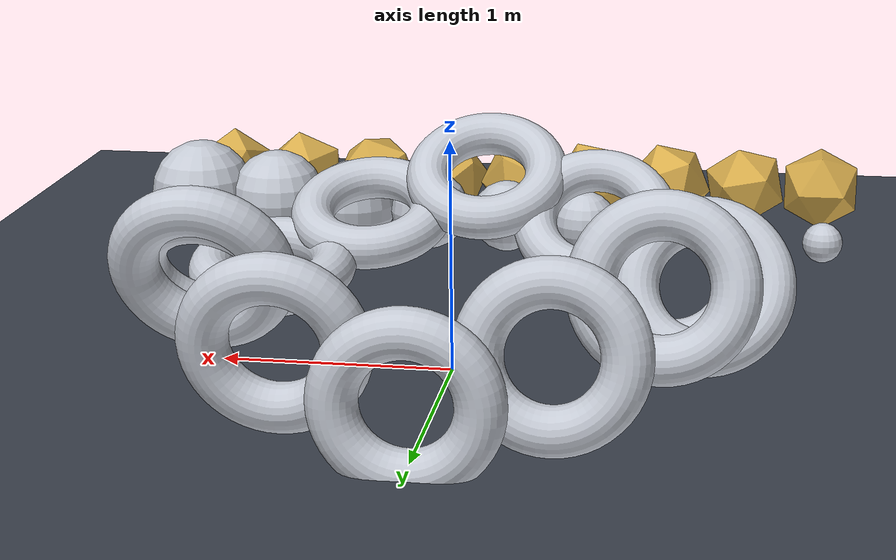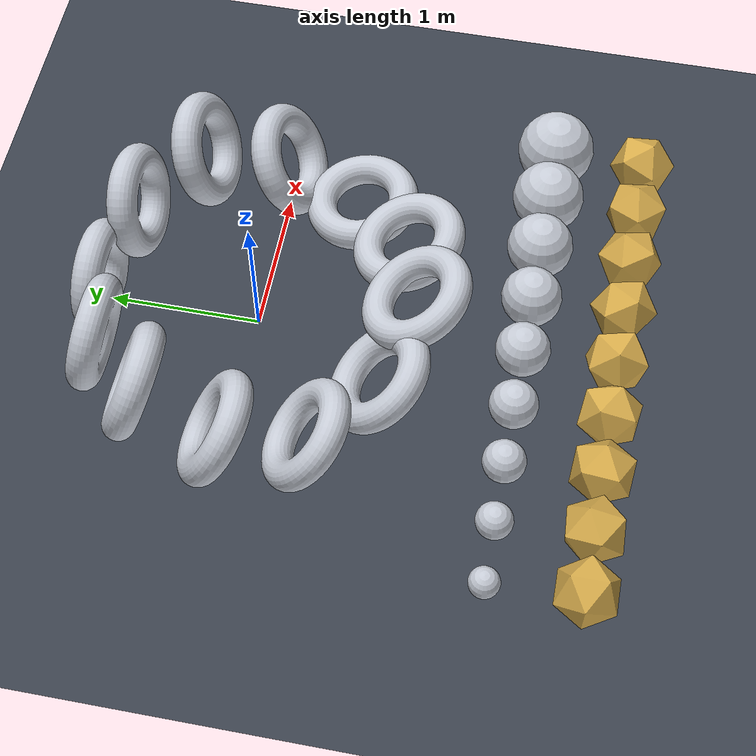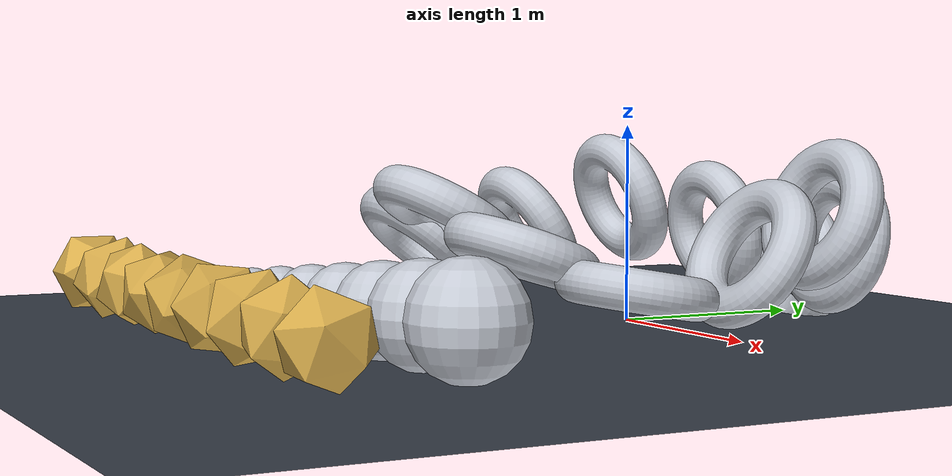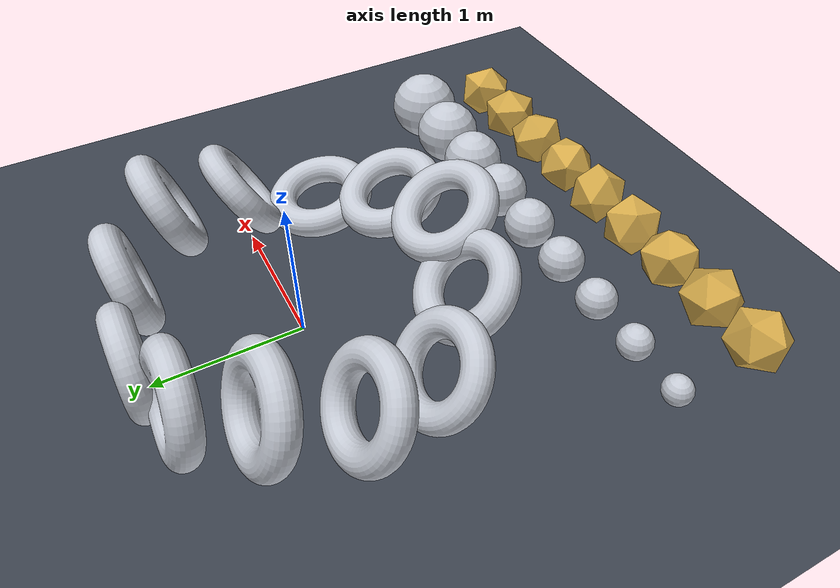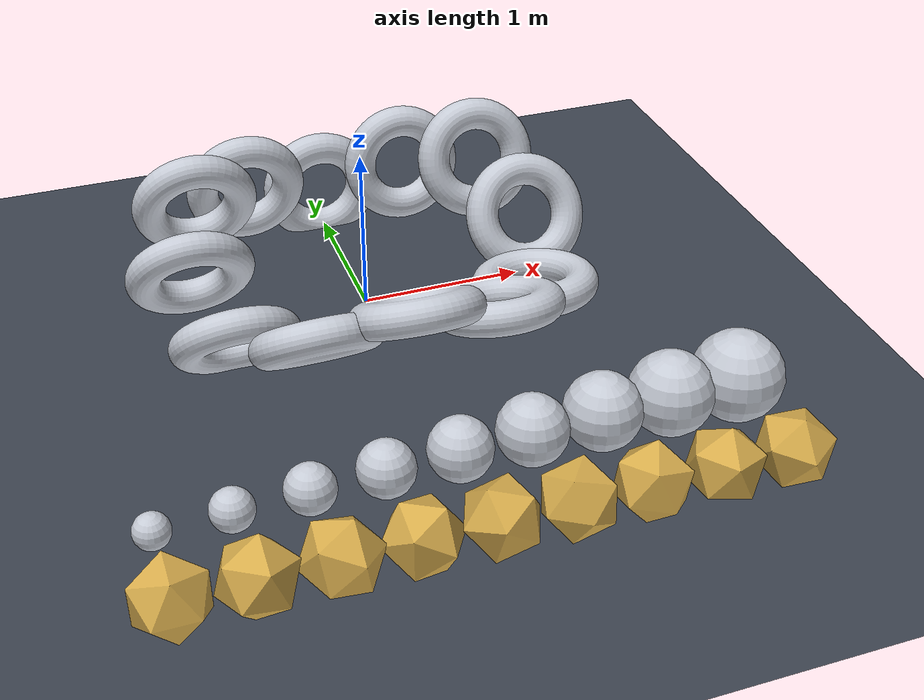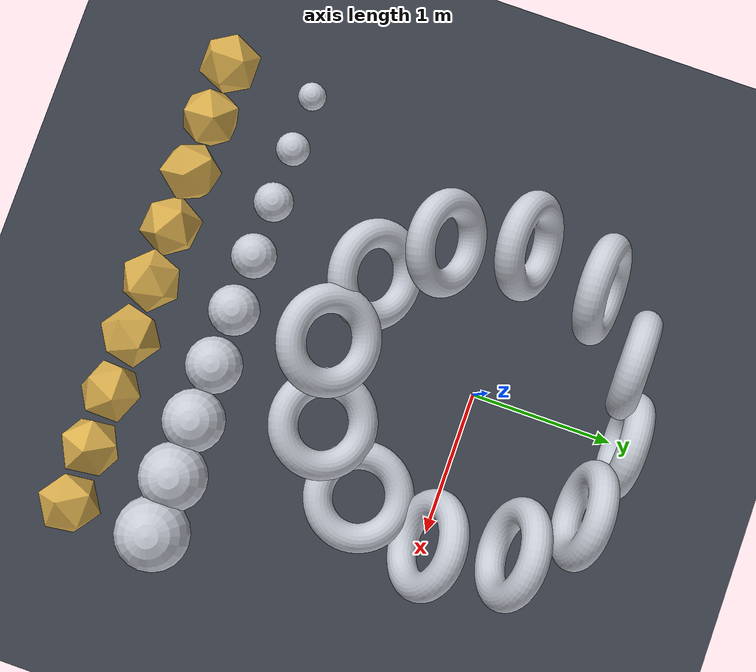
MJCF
<mujoco model="dense_mesh">
  <compiler angle="degree" autolimits="true"/>

  <visual>
    <headlight ambient="0.22 0.22 0.22" diffuse="0.4 0.4 0.4" specular="0.5 0.5 0.5"/>
    <quality shadowsize="4096" numslices="64" numstacks="32" numquads="8"/>
    <map znear="0.02" zfar="40" shadowclip="1.2" shadowscale="0.7"/>
  </visual>

  <asset>
    <texture name="grid" type="2d" builtin="checker" width="512" height="512"
             rgb1="0.18 0.20 0.24" rgb2="0.28 0.31 0.36"/>
    <material name="grid" texture="grid" texrepeat="1 1" texuniform="true"/>

    <material name="chrome" rgba="0.78 0.80 0.84 1" specular="0.95" shininess="0.92"/>
    <material name="brass" rgba="0.85 0.68 0.30 1" specular="0.9" shininess="0.85"/>

    <mesh name="torus"
          vertex="0.38000 0.00000 0.00000  0.37659 0.00000 0.02588  0.36660 0.00000 0.05000  0.35071 0.00000 0.07071  0.33000 0.00000 0.08660  0.30588 0.00000 0.09659
            0.28000 0.00000 0.10000  0.25412 0.00000 0.09659  0.23000 0.00000 0.08660  0.20929 0.00000 0.07071  0.19340 0.00000 0.05000  0.18341 0.00000 0.02588
            0.18000 0.00000 0.00000  0.18341 0.00000 -0.02588  0.19340 0.00000 -0.05000  0.20929 0.00000 -0.07071  0.23000 0.00000 -0.08660  0.25412 0.00000 -0.09659
            0.28000 0.00000 -0.10000  0.30588 0.00000 -0.09659  0.33000 0.00000 -0.08660  0.35071 0.00000 -0.07071  0.36660 0.00000 -0.05000  0.37659 0.00000 -0.02588
            0.37675 0.04960 0.00000  0.37337 0.04916 0.02588  0.36347 0.04785 0.05000  0.34771 0.04578 0.07071  0.32718 0.04307 0.08660  0.30327 0.03993 0.09659
            0.27760 0.03655 0.10000  0.25194 0.03317 0.09659  0.22803 0.03002 0.08660  0.20750 0.02732 0.07071  0.19174 0.02524 0.05000  0.18184 0.02394 0.02588
            0.17846 0.02349 0.00000  0.18184 0.02394 -0.02588  0.19174 0.02524 -0.05000  0.20750 0.02732 -0.07071  0.22803 0.03002 -0.08660  0.25194 0.03317 -0.09659
            0.27760 0.03655 -0.10000  0.30327 0.03993 -0.09659  0.32718 0.04307 -0.08660  0.34771 0.04578 -0.07071  0.36347 0.04785 -0.05000  0.37337 0.04916 -0.02588
            0.36705 0.09835 0.00000  0.36376 0.09747 0.02588  0.35411 0.09488 0.05000  0.33876 0.09077 0.07071  0.31876 0.08541 0.08660  0.29546 0.07917 0.09659
            0.27046 0.07247 0.10000  0.24546 0.06577 0.09659  0.22216 0.05953 0.08660  0.20216 0.05417 0.07071  0.18681 0.05005 0.05000  0.17716 0.04747 0.02588
            0.17387 0.04659 0.00000  0.17716 0.04747 -0.02588  0.18681 0.05005 -0.05000  0.20216 0.05417 -0.07071  0.22216 0.05953 -0.08660  0.24546 0.06577 -0.09659
            0.27046 0.07247 -0.10000  0.29546 0.07917 -0.09659  0.31876 0.08541 -0.08660  0.33876 0.09077 -0.07071  0.35411 0.09488 -0.05000  0.36376 0.09747 -0.02588
            0.35107 0.14542 0.00000  0.34793 0.14412 0.02588  0.33870 0.14029 0.05000  0.32401 0.13421 0.07071  0.30488 0.12629 0.08660  0.28260 0.11706 0.09659
            0.25869 0.10715 0.10000  0.23477 0.09725 0.09659  0.21249 0.08802 0.08660  0.19336 0.08009 0.07071  0.17868 0.07401 0.05000  0.16945 0.07019 0.02588
            0.16630 0.06888 0.00000  0.16945 0.07019 -0.02588  0.17868 0.07401 -0.05000  0.19336 0.08009 -0.07071  0.21249 0.08802 -0.08660  0.23477 0.09725 -0.09659
            0.25869 0.10715 -0.10000  0.28260 0.11706 -0.09659  0.30488 0.12629 -0.08660  0.32401 0.13421 -0.07071  0.33870 0.14029 -0.05000  0.34793 0.14412 -0.02588
            0.32909 0.19000 0.00000  0.32614 0.18830 0.02588  0.31749 0.18330 0.05000  0.30372 0.17536 0.07071  0.28579 0.16500 0.08660  0.26490 0.15294 0.09659
            0.24249 0.14000 0.10000  0.22007 0.12706 0.09659  0.19919 0.11500 0.08660  0.18125 0.10464 0.07071  0.16749 0.09670 0.05000  0.15884 0.09170 0.02588
            0.15588 0.09000 0.00000  0.15884 0.09170 -0.02588  0.16749 0.09670 -0.05000  0.18125 0.10464 -0.07071  0.19919 0.11500 -0.08660  0.22007 0.12706 -0.09659
            0.24249 0.14000 -0.10000  0.26490 0.15294 -0.09659  0.28579 0.16500 -0.08660  0.30372 0.17536 -0.07071  0.31749 0.18330 -0.05000  0.32614 0.18830 -0.02588
            0.30147 0.23133 0.00000  0.29877 0.22926 0.02588  0.29085 0.22317 0.05000  0.27824 0.21350 0.07071  0.26181 0.20089 0.08660  0.24267 0.18621 0.09659
            0.22214 0.17045 0.10000  0.20161 0.15470 0.09659  0.18247 0.14002 0.08660  0.16604 0.12741 0.07071  0.15343 0.11773 0.05000  0.14551 0.11165 0.02588
            0.14280 0.10958 0.00000  0.14551 0.11165 -0.02588  0.15343 0.11773 -0.05000  0.16604 0.12741 -0.07071  0.18247 0.14002 -0.08660  0.20161 0.15470 -0.09659
            0.22214 0.17045 -0.10000  0.24267 0.18621 -0.09659  0.26181 0.20089 -0.08660  0.27824 0.21350 -0.07071  0.29085 0.22317 -0.05000  0.29877 0.22926 -0.02588
            0.26870 0.26870 0.00000  0.26629 0.26629 0.02588  0.25923 0.25923 0.05000  0.24799 0.24799 0.07071  0.23335 0.23335 0.08660  0.21629 0.21629 0.09659
            0.19799 0.19799 0.10000  0.17969 0.17969 0.09659  0.16263 0.16263 0.08660  0.14799 0.14799 0.07071  0.13675 0.13675 0.05000  0.12969 0.12969 0.02588
            0.12728 0.12728 0.00000  0.12969 0.12969 -0.02588  0.13675 0.13675 -0.05000  0.14799 0.14799 -0.07071  0.16263 0.16263 -0.08660  0.17969 0.17969 -0.09659
            0.19799 0.19799 -0.10000  0.21629 0.21629 -0.09659  0.23335 0.23335 -0.08660  0.24799 0.24799 -0.07071  0.25923 0.25923 -0.05000  0.26629 0.26629 -0.02588
            0.23133 0.30147 0.00000  0.22926 0.29877 0.02588  0.22317 0.29085 0.05000  0.21350 0.27824 0.07071  0.20089 0.26181 0.08660  0.18621 0.24267 0.09659
            0.17045 0.22214 0.10000  0.15470 0.20161 0.09659  0.14002 0.18247 0.08660  0.12741 0.16604 0.07071  0.11773 0.15343 0.05000  0.11165 0.14551 0.02588
            0.10958 0.14280 0.00000  0.11165 0.14551 -0.02588  0.11773 0.15343 -0.05000  0.12741 0.16604 -0.07071  0.14002 0.18247 -0.08660  0.15470 0.20161 -0.09659
            0.17045 0.22214 -0.10000  0.18621 0.24267 -0.09659  0.20089 0.26181 -0.08660  0.21350 0.27824 -0.07071  0.22317 0.29085 -0.05000  0.22926 0.29877 -0.02588
            0.19000 0.32909 0.00000  0.18830 0.32614 0.02588  0.18330 0.31749 0.05000  0.17536 0.30372 0.07071  0.16500 0.28579 0.08660  0.15294 0.26490 0.09659
            0.14000 0.24249 0.10000  0.12706 0.22007 0.09659  0.11500 0.19919 0.08660  0.10464 0.18125 0.07071  0.09670 0.16749 0.05000  0.09170 0.15884 0.02588
            0.09000 0.15588 0.00000  0.09170 0.15884 -0.02588  0.09670 0.16749 -0.05000  0.10464 0.18125 -0.07071  0.11500 0.19919 -0.08660  0.12706 0.22007 -0.09659
            0.14000 0.24249 -0.10000  0.15294 0.26490 -0.09659  0.16500 0.28579 -0.08660  0.17536 0.30372 -0.07071  0.18330 0.31749 -0.05000  0.18830 0.32614 -0.02588
            0.14542 0.35107 0.00000  0.14412 0.34793 0.02588  0.14029 0.33870 0.05000  0.13421 0.32401 0.07071  0.12629 0.30488 0.08660  0.11706 0.28260 0.09659
            0.10715 0.25869 0.10000  0.09725 0.23477 0.09659  0.08802 0.21249 0.08660  0.08009 0.19336 0.07071  0.07401 0.17868 0.05000  0.07019 0.16945 0.02588
            0.06888 0.16630 0.00000  0.07019 0.16945 -0.02588  0.07401 0.17868 -0.05000  0.08009 0.19336 -0.07071  0.08802 0.21249 -0.08660  0.09725 0.23477 -0.09659
            0.10715 0.25869 -0.10000  0.11706 0.28260 -0.09659  0.12629 0.30488 -0.08660  0.13421 0.32401 -0.07071  0.14029 0.33870 -0.05000  0.14412 0.34793 -0.02588
            0.09835 0.36705 0.00000  0.09747 0.36376 0.02588  0.09488 0.35411 0.05000  0.09077 0.33876 0.07071  0.08541 0.31876 0.08660  0.07917 0.29546 0.09659
            0.07247 0.27046 0.10000  0.06577 0.24546 0.09659  0.05953 0.22216 0.08660  0.05417 0.20216 0.07071  0.05005 0.18681 0.05000  0.04747 0.17716 0.02588
            0.04659 0.17387 0.00000  0.04747 0.17716 -0.02588  0.05005 0.18681 -0.05000  0.05417 0.20216 -0.07071  0.05953 0.22216 -0.08660  0.06577 0.24546 -0.09659
            0.07247 0.27046 -0.10000  0.07917 0.29546 -0.09659  0.08541 0.31876 -0.08660  0.09077 0.33876 -0.07071  0.09488 0.35411 -0.05000  0.09747 0.36376 -0.02588
            0.04960 0.37675 0.00000  0.04916 0.37337 0.02588  0.04785 0.36347 0.05000  0.04578 0.34771 0.07071  0.04307 0.32718 0.08660  0.03993 0.30327 0.09659
            0.03655 0.27760 0.10000  0.03317 0.25194 0.09659  0.03002 0.22803 0.08660  0.02732 0.20750 0.07071  0.02524 0.19174 0.05000  0.02394 0.18184 0.02588
            0.02349 0.17846 0.00000  0.02394 0.18184 -0.02588  0.02524 0.19174 -0.05000  0.02732 0.20750 -0.07071  0.03002 0.22803 -0.08660  0.03317 0.25194 -0.09659
            0.03655 0.27760 -0.10000  0.03993 0.30327 -0.09659  0.04307 0.32718 -0.08660  0.04578 0.34771 -0.07071  0.04785 0.36347 -0.05000  0.04916 0.37337 -0.02588
            0.00000 0.38000 0.00000  0.00000 0.37659 0.02588  0.00000 0.36660 0.05000  0.00000 0.35071 0.07071  0.00000 0.33000 0.08660  0.00000 0.30588 0.09659
            0.00000 0.28000 0.10000  0.00000 0.25412 0.09659  0.00000 0.23000 0.08660  0.00000 0.20929 0.07071  0.00000 0.19340 0.05000  0.00000 0.18341 0.02588
            0.00000 0.18000 0.00000  0.00000 0.18341 -0.02588  0.00000 0.19340 -0.05000  0.00000 0.20929 -0.07071  0.00000 0.23000 -0.08660  0.00000 0.25412 -0.09659
            0.00000 0.28000 -0.10000  0.00000 0.30588 -0.09659  0.00000 0.33000 -0.08660  0.00000 0.35071 -0.07071  0.00000 0.36660 -0.05000  0.00000 0.37659 -0.02588
            -0.04960 0.37675 0.00000  -0.04916 0.37337 0.02588  -0.04785 0.36347 0.05000  -0.04578 0.34771 0.07071  -0.04307 0.32718 0.08660  -0.03993 0.30327 0.09659
            -0.03655 0.27760 0.10000  -0.03317 0.25194 0.09659  -0.03002 0.22803 0.08660  -0.02732 0.20750 0.07071  -0.02524 0.19174 0.05000  -0.02394 0.18184 0.02588
            -0.02349 0.17846 0.00000  -0.02394 0.18184 -0.02588  -0.02524 0.19174 -0.05000  -0.02732 0.20750 -0.07071  -0.03002 0.22803 -0.08660  -0.03317 0.25194 -0.09659
            -0.03655 0.27760 -0.10000  -0.03993 0.30327 -0.09659  -0.04307 0.32718 -0.08660  -0.04578 0.34771 -0.07071  -0.04785 0.36347 -0.05000  -0.04916 0.37337 -0.02588
            -0.09835 0.36705 0.00000  -0.09747 0.36376 0.02588  -0.09488 0.35411 0.05000  -0.09077 0.33876 0.07071  -0.08541 0.31876 0.08660  -0.07917 0.29546 0.09659
            -0.07247 0.27046 0.10000  -0.06577 0.24546 0.09659  -0.05953 0.22216 0.08660  -0.05417 0.20216 0.07071  -0.05005 0.18681 0.05000  -0.04747 0.17716 0.02588
            -0.04659 0.17387 0.00000  -0.04747 0.17716 -0.02588  -0.05005 0.18681 -0.05000  -0.05417 0.20216 -0.07071  -0.05953 0.22216 -0.08660  -0.06577 0.24546 -0.09659
            -0.07247 0.27046 -0.10000  -0.07917 0.29546 -0.09659  -0.08541 0.31876 -0.08660  -0.09077 0.33876 -0.07071  -0.09488 0.35411 -0.05000  -0.09747 0.36376 -0.02588
            -0.14542 0.35107 0.00000  -0.14412 0.34793 0.02588  -0.14029 0.33870 0.05000  -0.13421 0.32401 0.07071  -0.12629 0.30488 0.08660  -0.11706 0.28260 0.09659
            -0.10715 0.25869 0.10000  -0.09725 0.23477 0.09659  -0.08802 0.21249 0.08660  -0.08009 0.19336 0.07071  -0.07401 0.17868 0.05000  -0.07019 0.16945 0.02588
            -0.06888 0.16630 0.00000  -0.07019 0.16945 -0.02588  -0.07401 0.17868 -0.05000  -0.08009 0.19336 -0.07071  -0.08802 0.21249 -0.08660  -0.09725 0.23477 -0.09659
            -0.10715 0.25869 -0.10000  -0.11706 0.28260 -0.09659  -0.12629 0.30488 -0.08660  -0.13421 0.32401 -0.07071  -0.14029 0.33870 -0.05000  -0.14412 0.34793 -0.02588
            -0.19000 0.32909 0.00000  -0.18830 0.32614 0.02588  -0.18330 0.31749 0.05000  -0.17536 0.30372 0.07071  -0.16500 0.28579 0.08660  -0.15294 0.26490 0.09659
            -0.14000 0.24249 0.10000  -0.12706 0.22007 0.09659  -0.11500 0.19919 0.08660  -0.10464 0.18125 0.07071  -0.09670 0.16749 0.05000  -0.09170 0.15884 0.02588
            -0.09000 0.15588 0.00000  -0.09170 0.15884 -0.02588  -0.09670 0.16749 -0.05000  -0.10464 0.18125 -0.07071  -0.11500 0.19919 -0.08660  -0.12706 0.22007 -0.09659
            -0.14000 0.24249 -0.10000  -0.15294 0.26490 -0.09659  -0.16500 0.28579 -0.08660  -0.17536 0.30372 -0.07071  -0.18330 0.31749 -0.05000  -0.18830 0.32614 -0.02588
            -0.23133 0.30147 0.00000  -0.22926 0.29877 0.02588  -0.22317 0.29085 0.05000  -0.21350 0.27824 0.07071  -0.20089 0.26181 0.08660  -0.18621 0.24267 0.09659
            -0.17045 0.22214 0.10000  -0.15470 0.20161 0.09659  -0.14002 0.18247 0.08660  -0.12741 0.16604 0.07071  -0.11773 0.15343 0.05000  -0.11165 0.14551 0.02588
            -0.10958 0.14280 0.00000  -0.11165 0.14551 -0.02588  -0.11773 0.15343 -0.05000  -0.12741 0.16604 -0.07071  -0.14002 0.18247 -0.08660  -0.15470 0.20161 -0.09659
            -0.17045 0.22214 -0.10000  -0.18621 0.24267 -0.09659  -0.20089 0.26181 -0.08660  -0.21350 0.27824 -0.07071  -0.22317 0.29085 -0.05000  -0.22926 0.29877 -0.02588
            -0.26870 0.26870 0.00000  -0.26629 0.26629 0.02588  -0.25923 0.25923 0.05000  -0.24799 0.24799 0.07071  -0.23335 0.23335 0.08660  -0.21629 0.21629 0.09659
            -0.19799 0.19799 0.10000  -0.17969 0.17969 0.09659  -0.16263 0.16263 0.08660  -0.14799 0.14799 0.07071  -0.13675 0.13675 0.05000  -0.12969 0.12969 0.02588
            -0.12728 0.12728 0.00000  -0.12969 0.12969 -0.02588  -0.13675 0.13675 -0.05000  -0.14799 0.14799 -0.07071  -0.16263 0.16263 -0.08660  -0.17969 0.17969 -0.09659
            -0.19799 0.19799 -0.10000  -0.21629 0.21629 -0.09659  -0.23335 0.23335 -0.08660  -0.24799 0.24799 -0.07071  -0.25923 0.25923 -0.05000  -0.26629 0.26629 -0.02588
            -0.30147 0.23133 0.00000  -0.29877 0.22926 0.02588  -0.29085 0.22317 0.05000  -0.27824 0.21350 0.07071  -0.26181 0.20089 0.08660  -0.24267 0.18621 0.09659
            -0.22214 0.17045 0.10000  -0.20161 0.15470 0.09659  -0.18247 0.14002 0.08660  -0.16604 0.12741 0.07071  -0.15343 0.11773 0.05000  -0.14551 0.11165 0.02588
            -0.14280 0.10958 0.00000  -0.14551 0.11165 -0.02588  -0.15343 0.11773 -0.05000  -0.16604 0.12741 -0.07071  -0.18247 0.14002 -0.08660  -0.20161 0.15470 -0.09659
            -0.22214 0.17045 -0.10000  -0.24267 0.18621 -0.09659  -0.26181 0.20089 -0.08660  -0.27824 0.21350 -0.07071  -0.29085 0.22317 -0.05000  -0.29877 0.22926 -0.02588
            -0.32909 0.19000 0.00000  -0.32614 0.18830 0.02588  -0.31749 0.18330 0.05000  -0.30372 0.17536 0.07071  -0.28579 0.16500 0.08660  -0.26490 0.15294 0.09659
            -0.24249 0.14000 0.10000  -0.22007 0.12706 0.09659  -0.19919 0.11500 0.08660  -0.18125 0.10464 0.07071  -0.16749 0.09670 0.05000  -0.15884 0.09170 0.02588
            -0.15588 0.09000 0.00000  -0.15884 0.09170 -0.02588  -0.16749 0.09670 -0.05000  -0.18125 0.10464 -0.07071  -0.19919 0.11500 -0.08660  -0.22007 0.12706 -0.09659
            -0.24249 0.14000 -0.10000  -0.26490 0.15294 -0.09659  -0.28579 0.16500 -0.08660  -0.30372 0.17536 -0.07071  -0.31749 0.18330 -0.05000  -0.32614 0.18830 -0.02588
            -0.35107 0.14542 0.00000  -0.34793 0.14412 0.02588  -0.33870 0.14029 0.05000  -0.32401 0.13421 0.07071  -0.30488 0.12629 0.08660  -0.28260 0.11706 0.09659
            -0.25869 0.10715 0.10000  -0.23477 0.09725 0.09659  -0.21249 0.08802 0.08660  -0.19336 0.08009 0.07071  -0.17868 0.07401 0.05000  -0.16945 0.07019 0.02588
            -0.16630 0.06888 0.00000  -0.16945 0.07019 -0.02588  -0.17868 0.07401 -0.05000  -0.19336 0.08009 -0.07071  -0.21249 0.08802 -0.08660  -0.23477 0.09725 -0.09659
            -0.25869 0.10715 -0.10000  -0.28260 0.11706 -0.09659  -0.30488 0.12629 -0.08660  -0.32401 0.13421 -0.07071  -0.33870 0.14029 -0.05000  -0.34793 0.14412 -0.02588
            -0.36705 0.09835 0.00000  -0.36376 0.09747 0.02588  -0.35411 0.09488 0.05000  -0.33876 0.09077 0.07071  -0.31876 0.08541 0.08660  -0.29546 0.07917 0.09659
            -0.27046 0.07247 0.10000  -0.24546 0.06577 0.09659  -0.22216 0.05953 0.08660  -0.20216 0.05417 0.07071  -0.18681 0.05005 0.05000  -0.17716 0.04747 0.02588
            -0.17387 0.04659 0.00000  -0.17716 0.04747 -0.02588  -0.18681 0.05005 -0.05000  -0.20216 0.05417 -0.07071  -0.22216 0.05953 -0.08660  -0.24546 0.06577 -0.09659
            -0.27046 0.07247 -0.10000  -0.29546 0.07917 -0.09659  -0.31876 0.08541 -0.08660  -0.33876 0.09077 -0.07071  -0.35411 0.09488 -0.05000  -0.36376 0.09747 -0.02588
            -0.37675 0.04960 0.00000  -0.37337 0.04916 0.02588  -0.36347 0.04785 0.05000  -0.34771 0.04578 0.07071  -0.32718 0.04307 0.08660  -0.30327 0.03993 0.09659
            -0.27760 0.03655 0.10000  -0.25194 0.03317 0.09659  -0.22803 0.03002 0.08660  -0.20750 0.02732 0.07071  -0.19174 0.02524 0.05000  -0.18184 0.02394 0.02588
            -0.17846 0.02349 0.00000  -0.18184 0.02394 -0.02588  -0.19174 0.02524 -0.05000  -0.20750 0.02732 -0.07071  -0.22803 0.03002 -0.08660  -0.25194 0.03317 -0.09659
            -0.27760 0.03655 -0.10000  -0.30327 0.03993 -0.09659  -0.32718 0.04307 -0.08660  -0.34771 0.04578 -0.07071  -0.36347 0.04785 -0.05000  -0.37337 0.04916 -0.02588
            -0.38000 0.00000 0.00000  -0.37659 0.00000 0.02588  -0.36660 0.00000 0.05000  -0.35071 0.00000 0.07071  -0.33000 0.00000 0.08660  -0.30588 0.00000 0.09659
            -0.28000 0.00000 0.10000  -0.25412 0.00000 0.09659  -0.23000 0.00000 0.08660  -0.20929 0.00000 0.07071  -0.19340 0.00000 0.05000  -0.18341 0.00000 0.02588
            -0.18000 0.00000 0.00000  -0.18341 0.00000 -0.02588  -0.19340 0.00000 -0.05000  -0.20929 0.00000 -0.07071  -0.23000 0.00000 -0.08660  -0.25412 0.00000 -0.09659
            -0.28000 0.00000 -0.10000  -0.30588 0.00000 -0.09659  -0.33000 0.00000 -0.08660  -0.35071 0.00000 -0.07071  -0.36660 0.00000 -0.05000  -0.37659 0.00000 -0.02588
            -0.37675 -0.04960 0.00000  -0.37337 -0.04916 0.02588  -0.36347 -0.04785 0.05000  -0.34771 -0.04578 0.07071  -0.32718 -0.04307 0.08660  -0.30327 -0.03993 0.09659
            -0.27760 -0.03655 0.10000  -0.25194 -0.03317 0.09659  -0.22803 -0.03002 0.08660  -0.20750 -0.02732 0.07071  -0.19174 -0.02524 0.05000  -0.18184 -0.02394 0.02588
            -0.17846 -0.02349 0.00000  -0.18184 -0.02394 -0.02588  -0.19174 -0.02524 -0.05000  -0.20750 -0.02732 -0.07071  -0.22803 -0.03002 -0.08660  -0.25194 -0.03317 -0.09659
            -0.27760 -0.03655 -0.10000  -0.30327 -0.03993 -0.09659  -0.32718 -0.04307 -0.08660  -0.34771 -0.04578 -0.07071  -0.36347 -0.04785 -0.05000  -0.37337 -0.04916 -0.02588
            -0.36705 -0.09835 0.00000  -0.36376 -0.09747 0.02588  -0.35411 -0.09488 0.05000  -0.33876 -0.09077 0.07071  -0.31876 -0.08541 0.08660  -0.29546 -0.07917 0.09659
            -0.27046 -0.07247 0.10000  -0.24546 -0.06577 0.09659  -0.22216 -0.05953 0.08660  -0.20216 -0.05417 0.07071  -0.18681 -0.05005 0.05000  -0.17716 -0.04747 0.02588
            -0.17387 -0.04659 0.00000  -0.17716 -0.04747 -0.02588  -0.18681 -0.05005 -0.05000  -0.20216 -0.05417 -0.07071  -0.22216 -0.05953 -0.08660  -0.24546 -0.06577 -0.09659
            -0.27046 -0.07247 -0.10000  -0.29546 -0.07917 -0.09659  -0.31876 -0.08541 -0.08660  -0.33876 -0.09077 -0.07071  -0.35411 -0.09488 -0.05000  -0.36376 -0.09747 -0.02588
            -0.35107 -0.14542 0.00000  -0.34793 -0.14412 0.02588  -0.33870 -0.14029 0.05000  -0.32401 -0.13421 0.07071  -0.30488 -0.12629 0.08660  -0.28260 -0.11706 0.09659
            -0.25869 -0.10715 0.10000  -0.23477 -0.09725 0.09659  -0.21249 -0.08802 0.08660  -0.19336 -0.08009 0.07071  -0.17868 -0.07401 0.05000  -0.16945 -0.07019 0.02588
            -0.16630 -0.06888 0.00000  -0.16945 -0.07019 -0.02588  -0.17868 -0.07401 -0.05000  -0.19336 -0.08009 -0.07071  -0.21249 -0.08802 -0.08660  -0.23477 -0.09725 -0.09659
            -0.25869 -0.10715 -0.10000  -0.28260 -0.11706 -0.09659  -0.30488 -0.12629 -0.08660  -0.32401 -0.13421 -0.07071  -0.33870 -0.14029 -0.05000  -0.34793 -0.14412 -0.02588
            -0.32909 -0.19000 0.00000  -0.32614 -0.18830 0.02588  -0.31749 -0.18330 0.05000  -0.30372 -0.17536 0.07071  -0.28579 -0.16500 0.08660  -0.26490 -0.15294 0.09659
            -0.24249 -0.14000 0.10000  -0.22007 -0.12706 0.09659  -0.19919 -0.11500 0.08660  -0.18125 -0.10464 0.07071  -0.16749 -0.09670 0.05000  -0.15884 -0.09170 0.02588
            -0.15588 -0.09000 0.00000  -0.15884 -0.09170 -0.02588  -0.16749 -0.09670 -0.05000  -0.18125 -0.10464 -0.07071  -0.19919 -0.11500 -0.08660  -0.22007 -0.12706 -0.09659
            -0.24249 -0.14000 -0.10000  -0.26490 -0.15294 -0.09659  -0.28579 -0.16500 -0.08660  -0.30372 -0.17536 -0.07071  -0.31749 -0.18330 -0.05000  -0.32614 -0.18830 -0.02588
            -0.30147 -0.23133 0.00000  -0.29877 -0.22926 0.02588  -0.29085 -0.22317 0.05000  -0.27824 -0.21350 0.07071  -0.26181 -0.20089 0.08660  -0.24267 -0.18621 0.09659
            -0.22214 -0.17045 0.10000  -0.20161 -0.15470 0.09659  -0.18247 -0.14002 0.08660  -0.16604 -0.12741 0.07071  -0.15343 -0.11773 0.05000  -0.14551 -0.11165 0.02588
            -0.14280 -0.10958 0.00000  -0.14551 -0.11165 -0.02588  -0.15343 -0.11773 -0.05000  -0.16604 -0.12741 -0.07071  -0.18247 -0.14002 -0.08660  -0.20161 -0.15470 -0.09659
            -0.22214 -0.17045 -0.10000  -0.24267 -0.18621 -0.09659  -0.26181 -0.20089 -0.08660  -0.27824 -0.21350 -0.07071  -0.29085 -0.22317 -0.05000  -0.29877 -0.22926 -0.02588
            -0.26870 -0.26870 0.00000  -0.26629 -0.26629 0.02588  -0.25923 -0.25923 0.05000  -0.24799 -0.24799 0.07071  -0.23335 -0.23335 0.08660  -0.21629 -0.21629 0.09659
            -0.19799 -0.19799 0.10000  -0.17969 -0.17969 0.09659  -0.16263 -0.16263 0.08660  -0.14799 -0.14799 0.07071  -0.13675 -0.13675 0.05000  -0.12969 -0.12969 0.02588
            -0.12728 -0.12728 0.00000  -0.12969 -0.12969 -0.02588  -0.13675 -0.13675 -0.05000  -0.14799 -0.14799 -0.07071  -0.16263 -0.16263 -0.08660  -0.17969 -0.17969 -0.09659
            -0.19799 -0.19799 -0.10000  -0.21629 -0.21629 -0.09659  -0.23335 -0.23335 -0.08660  -0.24799 -0.24799 -0.07071  -0.25923 -0.25923 -0.05000  -0.26629 -0.26629 -0.02588
            -0.23133 -0.30147 0.00000  -0.22926 -0.29877 0.02588  -0.22317 -0.29085 0.05000  -0.21350 -0.27824 0.07071  -0.20089 -0.26181 0.08660  -0.18621 -0.24267 0.09659
            -0.17045 -0.22214 0.10000  -0.15470 -0.20161 0.09659  -0.14002 -0.18247 0.08660  -0.12741 -0.16604 0.07071  -0.11773 -0.15343 0.05000  -0.11165 -0.14551 0.02588
            -0.10958 -0.14280 0.00000  -0.11165 -0.14551 -0.02588  -0.11773 -0.15343 -0.05000  -0.12741 -0.16604 -0.07071  -0.14002 -0.18247 -0.08660  -0.15470 -0.20161 -0.09659
            -0.17045 -0.22214 -0.10000  -0.18621 -0.24267 -0.09659  -0.20089 -0.26181 -0.08660  -0.21350 -0.27824 -0.07071  -0.22317 -0.29085 -0.05000  -0.22926 -0.29877 -0.02588
            -0.19000 -0.32909 0.00000  -0.18830 -0.32614 0.02588  -0.18330 -0.31749 0.05000  -0.17536 -0.30372 0.07071  -0.16500 -0.28579 0.08660  -0.15294 -0.26490 0.09659
            -0.14000 -0.24249 0.10000  -0.12706 -0.22007 0.09659  -0.11500 -0.19919 0.08660  -0.10464 -0.18125 0.07071  -0.09670 -0.16749 0.05000  -0.09170 -0.15884 0.02588
            -0.09000 -0.15588 0.00000  -0.09170 -0.15884 -0.02588  -0.09670 -0.16749 -0.05000  -0.10464 -0.18125 -0.07071  -0.11500 -0.19919 -0.08660  -0.12706 -0.22007 -0.09659
            -0.14000 -0.24249 -0.10000  -0.15294 -0.26490 -0.09659  -0.16500 -0.28579 -0.08660  -0.17536 -0.30372 -0.07071  -0.18330 -0.31749 -0.05000  -0.18830 -0.32614 -0.02588
            -0.14542 -0.35107 0.00000  -0.14412 -0.34793 0.02588  -0.14029 -0.33870 0.05000  -0.13421 -0.32401 0.07071  -0.12629 -0.30488 0.08660  -0.11706 -0.28260 0.09659
            -0.10715 -0.25869 0.10000  -0.09725 -0.23477 0.09659  -0.08802 -0.21249 0.08660  -0.08009 -0.19336 0.07071  -0.07401 -0.17868 0.05000  -0.07019 -0.16945 0.02588
            -0.06888 -0.16630 0.00000  -0.07019 -0.16945 -0.02588  -0.07401 -0.17868 -0.05000  -0.08009 -0.19336 -0.07071  -0.08802 -0.21249 -0.08660  -0.09725 -0.23477 -0.09659
            -0.10715 -0.25869 -0.10000  -0.11706 -0.28260 -0.09659  -0.12629 -0.30488 -0.08660  -0.13421 -0.32401 -0.07071  -0.14029 -0.33870 -0.05000  -0.14412 -0.34793 -0.02588
            -0.09835 -0.36705 0.00000  -0.09747 -0.36376 0.02588  -0.09488 -0.35411 0.05000  -0.09077 -0.33876 0.07071  -0.08541 -0.31876 0.08660  -0.07917 -0.29546 0.09659
            -0.07247 -0.27046 0.10000  -0.06577 -0.24546 0.09659  -0.05953 -0.22216 0.08660  -0.05417 -0.20216 0.07071  -0.05005 -0.18681 0.05000  -0.04747 -0.17716 0.02588
            -0.04659 -0.17387 0.00000  -0.04747 -0.17716 -0.02588  -0.05005 -0.18681 -0.05000  -0.05417 -0.20216 -0.07071  -0.05953 -0.22216 -0.08660  -0.06577 -0.24546 -0.09659
            -0.07247 -0.27046 -0.10000  -0.07917 -0.29546 -0.09659  -0.08541 -0.31876 -0.08660  -0.09077 -0.33876 -0.07071  -0.09488 -0.35411 -0.05000  -0.09747 -0.36376 -0.02588
            -0.04960 -0.37675 0.00000  -0.04916 -0.37337 0.02588  -0.04785 -0.36347 0.05000  -0.04578 -0.34771 0.07071  -0.04307 -0.32718 0.08660  -0.03993 -0.30327 0.09659
            -0.03655 -0.27760 0.10000  -0.03317 -0.25194 0.09659  -0.03002 -0.22803 0.08660  -0.02732 -0.20750 0.07071  -0.02524 -0.19174 0.05000  -0.02394 -0.18184 0.02588
            -0.02349 -0.17846 0.00000  -0.02394 -0.18184 -0.02588  -0.02524 -0.19174 -0.05000  -0.02732 -0.20750 -0.07071  -0.03002 -0.22803 -0.08660  -0.03317 -0.25194 -0.09659
            -0.03655 -0.27760 -0.10000  -0.03993 -0.30327 -0.09659  -0.04307 -0.32718 -0.08660  -0.04578 -0.34771 -0.07071  -0.04785 -0.36347 -0.05000  -0.04916 -0.37337 -0.02588
            -0.00000 -0.38000 0.00000  -0.00000 -0.37659 0.02588  -0.00000 -0.36660 0.05000  -0.00000 -0.35071 0.07071  -0.00000 -0.33000 0.08660  -0.00000 -0.30588 0.09659
            -0.00000 -0.28000 0.10000  -0.00000 -0.25412 0.09659  -0.00000 -0.23000 0.08660  -0.00000 -0.20929 0.07071  -0.00000 -0.19340 0.05000  -0.00000 -0.18341 0.02588
            -0.00000 -0.18000 0.00000  -0.00000 -0.18341 -0.02588  -0.00000 -0.19340 -0.05000  -0.00000 -0.20929 -0.07071  -0.00000 -0.23000 -0.08660  -0.00000 -0.25412 -0.09659
            -0.00000 -0.28000 -0.10000  -0.00000 -0.30588 -0.09659  -0.00000 -0.33000 -0.08660  -0.00000 -0.35071 -0.07071  -0.00000 -0.36660 -0.05000  -0.00000 -0.37659 -0.02588
            0.04960 -0.37675 0.00000  0.04916 -0.37337 0.02588  0.04785 -0.36347 0.05000  0.04578 -0.34771 0.07071  0.04307 -0.32718 0.08660  0.03993 -0.30327 0.09659
            0.03655 -0.27760 0.10000  0.03317 -0.25194 0.09659  0.03002 -0.22803 0.08660  0.02732 -0.20750 0.07071  0.02524 -0.19174 0.05000  0.02394 -0.18184 0.02588
            0.02349 -0.17846 0.00000  0.02394 -0.18184 -0.02588  0.02524 -0.19174 -0.05000  0.02732 -0.20750 -0.07071  0.03002 -0.22803 -0.08660  0.03317 -0.25194 -0.09659
            0.03655 -0.27760 -0.10000  0.03993 -0.30327 -0.09659  0.04307 -0.32718 -0.08660  0.04578 -0.34771 -0.07071  0.04785 -0.36347 -0.05000  0.04916 -0.37337 -0.02588
            0.09835 -0.36705 0.00000  0.09747 -0.36376 0.02588  0.09488 -0.35411 0.05000  0.09077 -0.33876 0.07071  0.08541 -0.31876 0.08660  0.07917 -0.29546 0.09659
            0.07247 -0.27046 0.10000  0.06577 -0.24546 0.09659  0.05953 -0.22216 0.08660  0.05417 -0.20216 0.07071  0.05005 -0.18681 0.05000  0.04747 -0.17716 0.02588
            0.04659 -0.17387 0.00000  0.04747 -0.17716 -0.02588  0.05005 -0.18681 -0.05000  0.05417 -0.20216 -0.07071  0.05953 -0.22216 -0.08660  0.06577 -0.24546 -0.09659
            0.07247 -0.27046 -0.10000  0.07917 -0.29546 -0.09659  0.08541 -0.31876 -0.08660  0.09077 -0.33876 -0.07071  0.09488 -0.35411 -0.05000  0.09747 -0.36376 -0.02588
            0.14542 -0.35107 0.00000  0.14412 -0.34793 0.02588  0.14029 -0.33870 0.05000  0.13421 -0.32401 0.07071  0.12629 -0.30488 0.08660  0.11706 -0.28260 0.09659
            0.10715 -0.25869 0.10000  0.09725 -0.23477 0.09659  0.08802 -0.21249 0.08660  0.08009 -0.19336 0.07071  0.07401 -0.17868 0.05000  0.07019 -0.16945 0.02588
            0.06888 -0.16630 0.00000  0.07019 -0.16945 -0.02588  0.07401 -0.17868 -0.05000  0.08009 -0.19336 -0.07071  0.08802 -0.21249 -0.08660  0.09725 -0.23477 -0.09659
            0.10715 -0.25869 -0.10000  0.11706 -0.28260 -0.09659  0.12629 -0.30488 -0.08660  0.13421 -0.32401 -0.07071  0.14029 -0.33870 -0.05000  0.14412 -0.34793 -0.02588
            0.19000 -0.32909 0.00000  0.18830 -0.32614 0.02588  0.18330 -0.31749 0.05000  0.17536 -0.30372 0.07071  0.16500 -0.28579 0.08660  0.15294 -0.26490 0.09659
            0.14000 -0.24249 0.10000  0.12706 -0.22007 0.09659  0.11500 -0.19919 0.08660  0.10464 -0.18125 0.07071  0.09670 -0.16749 0.05000  0.09170 -0.15884 0.02588
            0.09000 -0.15588 0.00000  0.09170 -0.15884 -0.02588  0.09670 -0.16749 -0.05000  0.10464 -0.18125 -0.07071  0.11500 -0.19919 -0.08660  0.12706 -0.22007 -0.09659
            0.14000 -0.24249 -0.10000  0.15294 -0.26490 -0.09659  0.16500 -0.28579 -0.08660  0.17536 -0.30372 -0.07071  0.18330 -0.31749 -0.05000  0.18830 -0.32614 -0.02588
            0.23133 -0.30147 0.00000  0.22926 -0.29877 0.02588  0.22317 -0.29085 0.05000  0.21350 -0.27824 0.07071  0.20089 -0.26181 0.08660  0.18621 -0.24267 0.09659
            0.17045 -0.22214 0.10000  0.15470 -0.20161 0.09659  0.14002 -0.18247 0.08660  0.12741 -0.16604 0.07071  0.11773 -0.15343 0.05000  0.11165 -0.14551 0.02588
            0.10958 -0.14280 0.00000  0.11165 -0.14551 -0.02588  0.11773 -0.15343 -0.05000  0.12741 -0.16604 -0.07071  0.14002 -0.18247 -0.08660  0.15470 -0.20161 -0.09659
            0.17045 -0.22214 -0.10000  0.18621 -0.24267 -0.09659  0.20089 -0.26181 -0.08660  0.21350 -0.27824 -0.07071  0.22317 -0.29085 -0.05000  0.22926 -0.29877 -0.02588
            0.26870 -0.26870 0.00000  0.26629 -0.26629 0.02588  0.25923 -0.25923 0.05000  0.24799 -0.24799 0.07071  0.23335 -0.23335 0.08660  0.21629 -0.21629 0.09659
            0.19799 -0.19799 0.10000  0.17969 -0.17969 0.09659  0.16263 -0.16263 0.08660  0.14799 -0.14799 0.07071  0.13675 -0.13675 0.05000  0.12969 -0.12969 0.02588
            0.12728 -0.12728 0.00000  0.12969 -0.12969 -0.02588  0.13675 -0.13675 -0.05000  0.14799 -0.14799 -0.07071  0.16263 -0.16263 -0.08660  0.17969 -0.17969 -0.09659
            0.19799 -0.19799 -0.10000  0.21629 -0.21629 -0.09659  0.23335 -0.23335 -0.08660  0.24799 -0.24799 -0.07071  0.25923 -0.25923 -0.05000  0.26629 -0.26629 -0.02588
            0.30147 -0.23133 0.00000  0.29877 -0.22926 0.02588  0.29085 -0.22317 0.05000  0.27824 -0.21350 0.07071  0.26181 -0.20089 0.08660  0.24267 -0.18621 0.09659
            0.22214 -0.17045 0.10000  0.20161 -0.15470 0.09659  0.18247 -0.14002 0.08660  0.16604 -0.12741 0.07071  0.15343 -0.11773 0.05000  0.14551 -0.11165 0.02588
            0.14280 -0.10958 0.00000  0.14551 -0.11165 -0.02588  0.15343 -0.11773 -0.05000  0.16604 -0.12741 -0.07071  0.18247 -0.14002 -0.08660  0.20161 -0.15470 -0.09659
            0.22214 -0.17045 -0.10000  0.24267 -0.18621 -0.09659  0.26181 -0.20089 -0.08660  0.27824 -0.21350 -0.07071  0.29085 -0.22317 -0.05000  0.29877 -0.22926 -0.02588
            0.32909 -0.19000 0.00000  0.32614 -0.18830 0.02588  0.31749 -0.18330 0.05000  0.30372 -0.17536 0.07071  0.28579 -0.16500 0.08660  0.26490 -0.15294 0.09659
            0.24249 -0.14000 0.10000  0.22007 -0.12706 0.09659  0.19919 -0.11500 0.08660  0.18125 -0.10464 0.07071  0.16749 -0.09670 0.05000  0.15884 -0.09170 0.02588
            0.15588 -0.09000 0.00000  0.15884 -0.09170 -0.02588  0.16749 -0.09670 -0.05000  0.18125 -0.10464 -0.07071  0.19919 -0.11500 -0.08660  0.22007 -0.12706 -0.09659
            0.24249 -0.14000 -0.10000  0.26490 -0.15294 -0.09659  0.28579 -0.16500 -0.08660  0.30372 -0.17536 -0.07071  0.31749 -0.18330 -0.05000  0.32614 -0.18830 -0.02588
            0.35107 -0.14542 0.00000  0.34793 -0.14412 0.02588  0.33870 -0.14029 0.05000  0.32401 -0.13421 0.07071  0.30488 -0.12629 0.08660  0.28260 -0.11706 0.09659
            0.25869 -0.10715 0.10000  0.23477 -0.09725 0.09659  0.21249 -0.08802 0.08660  0.19336 -0.08009 0.07071  0.17868 -0.07401 0.05000  0.16945 -0.07019 0.02588
            0.16630 -0.06888 0.00000  0.16945 -0.07019 -0.02588  0.17868 -0.07401 -0.05000  0.19336 -0.08009 -0.07071  0.21249 -0.08802 -0.08660  0.23477 -0.09725 -0.09659
            0.25869 -0.10715 -0.10000  0.28260 -0.11706 -0.09659  0.30488 -0.12629 -0.08660  0.32401 -0.13421 -0.07071  0.33870 -0.14029 -0.05000  0.34793 -0.14412 -0.02588
            0.36705 -0.09835 0.00000  0.36376 -0.09747 0.02588  0.35411 -0.09488 0.05000  0.33876 -0.09077 0.07071  0.31876 -0.08541 0.08660  0.29546 -0.07917 0.09659
            0.27046 -0.07247 0.10000  0.24546 -0.06577 0.09659  0.22216 -0.05953 0.08660  0.20216 -0.05417 0.07071  0.18681 -0.05005 0.05000  0.17716 -0.04747 0.02588
            0.17387 -0.04659 0.00000  0.17716 -0.04747 -0.02588  0.18681 -0.05005 -0.05000  0.20216 -0.05417 -0.07071  0.22216 -0.05953 -0.08660  0.24546 -0.06577 -0.09659
            0.27046 -0.07247 -0.10000  0.29546 -0.07917 -0.09659  0.31876 -0.08541 -0.08660  0.33876 -0.09077 -0.07071  0.35411 -0.09488 -0.05000  0.36376 -0.09747 -0.02588
            0.37675 -0.04960 0.00000  0.37337 -0.04916 0.02588  0.36347 -0.04785 0.05000  0.34771 -0.04578 0.07071  0.32718 -0.04307 0.08660  0.30327 -0.03993 0.09659
            0.27760 -0.03655 0.10000  0.25194 -0.03317 0.09659  0.22803 -0.03002 0.08660  0.20750 -0.02732 0.07071  0.19174 -0.02524 0.05000  0.18184 -0.02394 0.02588
            0.17846 -0.02349 0.00000  0.18184 -0.02394 -0.02588  0.19174 -0.02524 -0.05000  0.20750 -0.02732 -0.07071  0.22803 -0.03002 -0.08660  0.25194 -0.03317 -0.09659
            0.27760 -0.03655 -0.10000  0.30327 -0.03993 -0.09659  0.32718 -0.04307 -0.08660  0.34771 -0.04578 -0.07071  0.36347 -0.04785 -0.05000  0.37337 -0.04916 -0.02588"
          face="0 24 25  0 25 1  1 25 26  1 26 2  2 26 27  2 27 3  3 27 28  3 28 4  4 28 29  4 29 5
            5 29 30  5 30 6  6 30 31  6 31 7  7 31 32  7 32 8  8 32 33  8 33 9  9 33 34  9 34 10
            10 34 35  10 35 11  11 35 36  11 36 12  12 36 37  12 37 13  13 37 38  13 38 14  14 38 39  14 39 15
            15 39 40  15 40 16  16 40 41  16 41 17  17 41 42  17 42 18  18 42 43  18 43 19  19 43 44  19 44 20
            20 44 45  20 45 21  21 45 46  21 46 22  22 46 47  22 47 23  23 47 24  23 24 0  24 48 49  24 49 25
            25 49 50  25 50 26  26 50 51  26 51 27  27 51 52  27 52 28  28 52 53  28 53 29  29 53 54  29 54 30
            30 54 55  30 55 31  31 55 56  31 56 32  32 56 57  32 57 33  33 57 58  33 58 34  34 58 59  34 59 35
            35 59 60  35 60 36  36 60 61  36 61 37  37 61 62  37 62 38  38 62 63  38 63 39  39 63 64  39 64 40
            40 64 65  40 65 41  41 65 66  41 66 42  42 66 67  42 67 43  43 67 68  43 68 44  44 68 69  44 69 45
            45 69 70  45 70 46  46 70 71  46 71 47  47 71 48  47 48 24  48 72 73  48 73 49  49 73 74  49 74 50
            50 74 75  50 75 51  51 75 76  51 76 52  52 76 77  52 77 53  53 77 78  53 78 54  54 78 79  54 79 55
            55 79 80  55 80 56  56 80 81  56 81 57  57 81 82  57 82 58  58 82 83  58 83 59  59 83 84  59 84 60
            60 84 85  60 85 61  61 85 86  61 86 62  62 86 87  62 87 63  63 87 88  63 88 64  64 88 89  64 89 65
            65 89 90  65 90 66  66 90 91  66 91 67  67 91 92  67 92 68  68 92 93  68 93 69  69 93 94  69 94 70
            70 94 95  70 95 71  71 95 72  71 72 48  72 96 97  72 97 73  73 97 98  73 98 74  74 98 99  74 99 75
            75 99 100  75 100 76  76 100 101  76 101 77  77 101 102  77 102 78  78 102 103  78 103 79  79 103 104  79 104 80
            80 104 105  80 105 81  81 105 106  81 106 82  82 106 107  82 107 83  83 107 108  83 108 84  84 108 109  84 109 85
            85 109 110  85 110 86  86 110 111  86 111 87  87 111 112  87 112 88  88 112 113  88 113 89  89 113 114  89 114 90
            90 114 115  90 115 91  91 115 116  91 116 92  92 116 117  92 117 93  93 117 118  93 118 94  94 118 119  94 119 95
            95 119 96  95 96 72  96 120 121  96 121 97  97 121 122  97 122 98  98 122 123  98 123 99  99 123 124  99 124 100
            100 124 125  100 125 101  101 125 126  101 126 102  102 126 127  102 127 103  103 127 128  103 128 104  104 128 129  104 129 105
            105 129 130  105 130 106  106 130 131  106 131 107  107 131 132  107 132 108  108 132 133  108 133 109  109 133 134  109 134 110
            110 134 135  110 135 111  111 135 136  111 136 112  112 136 137  112 137 113  113 137 138  113 138 114  114 138 139  114 139 115
            115 139 140  115 140 116  116 140 141  116 141 117  117 141 142  117 142 118  118 142 143  118 143 119  119 143 120  119 120 96
            120 144 145  120 145 121  121 145 146  121 146 122  122 146 147  122 147 123  123 147 148  123 148 124  124 148 149  124 149 125
            125 149 150  125 150 126  126 150 151  126 151 127  127 151 152  127 152 128  128 152 153  128 153 129  129 153 154  129 154 130
            130 154 155  130 155 131  131 155 156  131 156 132  132 156 157  132 157 133  133 157 158  133 158 134  134 158 159  134 159 135
            135 159 160  135 160 136  136 160 161  136 161 137  137 161 162  137 162 138  138 162 163  138 163 139  139 163 164  139 164 140
            140 164 165  140 165 141  141 165 166  141 166 142  142 166 167  142 167 143  143 167 144  143 144 120  144 168 169  144 169 145
            145 169 170  145 170 146  146 170 171  146 171 147  147 171 172  147 172 148  148 172 173  148 173 149  149 173 174  149 174 150
            150 174 175  150 175 151  151 175 176  151 176 152  152 176 177  152 177 153  153 177 178  153 178 154  154 178 179  154 179 155
            155 179 180  155 180 156  156 180 181  156 181 157  157 181 182  157 182 158  158 182 183  158 183 159  159 183 184  159 184 160
            160 184 185  160 185 161  161 185 186  161 186 162  162 186 187  162 187 163  163 187 188  163 188 164  164 188 189  164 189 165
            165 189 190  165 190 166  166 190 191  166 191 167  167 191 168  167 168 144  168 192 193  168 193 169  169 193 194  169 194 170
            170 194 195  170 195 171  171 195 196  171 196 172  172 196 197  172 197 173  173 197 198  173 198 174  174 198 199  174 199 175
            175 199 200  175 200 176  176 200 201  176 201 177  177 201 202  177 202 178  178 202 203  178 203 179  179 203 204  179 204 180
            180 204 205  180 205 181  181 205 206  181 206 182  182 206 207  182 207 183  183 207 208  183 208 184  184 208 209  184 209 185
            185 209 210  185 210 186  186 210 211  186 211 187  187 211 212  187 212 188  188 212 213  188 213 189  189 213 214  189 214 190
            190 214 215  190 215 191  191 215 192  191 192 168  192 216 217  192 217 193  193 217 218  193 218 194  194 218 219  194 219 195
            195 219 220  195 220 196  196 220 221  196 221 197  197 221 222  197 222 198  198 222 223  198 223 199  199 223 224  199 224 200
            200 224 225  200 225 201  201 225 226  201 226 202  202 226 227  202 227 203  203 227 228  203 228 204  204 228 229  204 229 205
            205 229 230  205 230 206  206 230 231  206 231 207  207 231 232  207 232 208  208 232 233  208 233 209  209 233 234  209 234 210
            210 234 235  210 235 211  211 235 236  211 236 212  212 236 237  212 237 213  213 237 238  213 238 214  214 238 239  214 239 215
            215 239 216  215 216 192  216 240 241  216 241 217  217 241 242  217 242 218  218 242 243  218 243 219  219 243 244  219 244 220
            220 244 245  220 245 221  221 245 246  221 246 222  222 246 247  222 247 223  223 247 248  223 248 224  224 248 249  224 249 225
            225 249 250  225 250 226  226 250 251  226 251 227  227 251 252  227 252 228  228 252 253  228 253 229  229 253 254  229 254 230
            230 254 255  230 255 231  231 255 256  231 256 232  232 256 257  232 257 233  233 257 258  233 258 234  234 258 259  234 259 235
            235 259 260  235 260 236  236 260 261  236 261 237  237 261 262  237 262 238  238 262 263  238 263 239  239 263 240  239 240 216
            240 264 265  240 265 241  241 265 266  241 266 242  242 266 267  242 267 243  243 267 268  243 268 244  244 268 269  244 269 245
            245 269 270  245 270 246  246 270 271  246 271 247  247 271 272  247 272 248  248 272 273  248 273 249  249 273 274  249 274 250
            250 274 275  250 275 251  251 275 276  251 276 252  252 276 277  252 277 253  253 277 278  253 278 254  254 278 279  254 279 255
            255 279 280  255 280 256  256 280 281  256 281 257  257 281 282  257 282 258  258 282 283  258 283 259  259 283 284  259 284 260
            260 284 285  260 285 261  261 285 286  261 286 262  262 286 287  262 287 263  263 287 264  263 264 240  264 288 289  264 289 265
            265 289 290  265 290 266  266 290 291  266 291 267  267 291 292  267 292 268  268 292 293  268 293 269  269 293 294  269 294 270
            270 294 295  270 295 271  271 295 296  271 296 272  272 296 297  272 297 273  273 297 298  273 298 274  274 298 299  274 299 275
            275 299 300  275 300 276  276 300 301  276 301 277  277 301 302  277 302 278  278 302 303  278 303 279  279 303 304  279 304 280
            280 304 305  280 305 281  281 305 306  281 306 282  282 306 307  282 307 283  283 307 308  283 308 284  284 308 309  284 309 285
            285 309 310  285 310 286  286 310 311  286 311 287  287 311 288  287 288 264  288 312 313  288 313 289  289 313 314  289 314 290
            290 314 315  290 315 291  291 315 316  291 316 292  292 316 317  292 317 293  293 317 318  293 318 294  294 318 319  294 319 295
            295 319 320  295 320 296  296 320 321  296 321 297  297 321 322  297 322 298  298 322 323  298 323 299  299 323 324  299 324 300
            300 324 325  300 325 301  301 325 326  301 326 302  302 326 327  302 327 303  303 327 328  303 328 304  304 328 329  304 329 305
            305 329 330  305 330 306  306 330 331  306 331 307  307 331 332  307 332 308  308 332 333  308 333 309  309 333 334  309 334 310
            310 334 335  310 335 311  311 335 312  311 312 288  312 336 337  312 337 313  313 337 338  313 338 314  314 338 339  314 339 315
            315 339 340  315 340 316  316 340 341  316 341 317  317 341 342  317 342 318  318 342 343  318 343 319  319 343 344  319 344 320
            320 344 345  320 345 321  321 345 346  321 346 322  322 346 347  322 347 323  323 347 348  323 348 324  324 348 349  324 349 325
            325 349 350  325 350 326  326 350 351  326 351 327  327 351 352  327 352 328  328 352 353  328 353 329  329 353 354  329 354 330
            330 354 355  330 355 331  331 355 356  331 356 332  332 356 357  332 357 333  333 357 358  333 358 334  334 358 359  334 359 335
            335 359 336  335 336 312  336 360 361  336 361 337  337 361 362  337 362 338  338 362 363  338 363 339  339 363 364  339 364 340
            340 364 365  340 365 341  341 365 366  341 366 342  342 366 367  342 367 343  343 367 368  343 368 344  344 368 369  344 369 345
            345 369 370  345 370 346  346 370 371  346 371 347  347 371 372  347 372 348  348 372 373  348 373 349  349 373 374  349 374 350
            350 374 375  350 375 351  351 375 376  351 376 352  352 376 377  352 377 353  353 377 378  353 378 354  354 378 379  354 379 355
            355 379 380  355 380 356  356 380 381  356 381 357  357 381 382  357 382 358  358 382 383  358 383 359  359 383 360  359 360 336
            360 384 385  360 385 361  361 385 386  361 386 362  362 386 387  362 387 363  363 387 388  363 388 364  364 388 389  364 389 365
            365 389 390  365 390 366  366 390 391  366 391 367  367 391 392  367 392 368  368 392 393  368 393 369  369 393 394  369 394 370
            370 394 395  370 395 371  371 395 396  371 396 372  372 396 397  372 397 373  373 397 398  373 398 374  374 398 399  374 399 375
            375 399 400  375 400 376  376 400 401  376 401 377  377 401 402  377 402 378  378 402 403  378 403 379  379 403 404  379 404 380
            380 404 405  380 405 381  381 405 406  381 406 382  382 406 407  382 407 383  383 407 384  383 384 360  384 408 409  384 409 385
            385 409 410  385 410 386  386 410 411  386 411 387  387 411 412  387 412 388  388 412 413  388 413 389  389 413 414  389 414 390
            390 414 415  390 415 391  391 415 416  391 416 392  392 416 417  392 417 393  393 417 418  393 418 394  394 418 419  394 419 395
            395 419 420  395 420 396  396 420 421  396 421 397  397 421 422  397 422 398  398 422 423  398 423 399  399 423 424  399 424 400
            400 424 425  400 425 401  401 425 426  401 426 402  402 426 427  402 427 403  403 427 428  403 428 404  404 428 429  404 429 405
            405 429 430  405 430 406  406 430 431  406 431 407  407 431 408  407 408 384  408 432 433  408 433 409  409 433 434  409 434 410
            410 434 435  410 435 411  411 435 436  411 436 412  412 436 437  412 437 413  413 437 438  413 438 414  414 438 439  414 439 415
            415 439 440  415 440 416  416 440 441  416 441 417  417 441 442  417 442 418  418 442 443  418 443 419  419 443 444  419 444 420
            420 444 445  420 445 421  421 445 446  421 446 422  422 446 447  422 447 423  423 447 448  423 448 424  424 448 449  424 449 425
            425 449 450  425 450 426  426 450 451  426 451 427  427 451 452  427 452 428  428 452 453  428 453 429  429 453 454  429 454 430
            430 454 455  430 455 431  431 455 432  431 432 408  432 456 457  432 457 433  433 457 458  433 458 434  434 458 459  434 459 435
            435 459 460  435 460 436  436 460 461  436 461 437  437 461 462  437 462 438  438 462 463  438 463 439  439 463 464  439 464 440
            440 464 465  440 465 441  441 465 466  441 466 442  442 466 467  442 467 443  443 467 468  443 468 444  444 468 469  444 469 445
            445 469 470  445 470 446  446 470 471  446 471 447  447 471 472  447 472 448  448 472 473  448 473 449  449 473 474  449 474 450
            450 474 475  450 475 451  451 475 476  451 476 452  452 476 477  452 477 453  453 477 478  453 478 454  454 478 479  454 479 455
            455 479 456  455 456 432  456 480 481  456 481 457  457 481 482  457 482 458  458 482 483  458 483 459  459 483 484  459 484 460
            460 484 485  460 485 461  461 485 486  461 486 462  462 486 487  462 487 463  463 487 488  463 488 464  464 488 489  464 489 465
            465 489 490  465 490 466  466 490 491  466 491 467  467 491 492  467 492 468  468 492 493  468 493 469  469 493 494  469 494 470
            470 494 495  470 495 471  471 495 496  471 496 472  472 496 497  472 497 473  473 497 498  473 498 474  474 498 499  474 499 475
            475 499 500  475 500 476  476 500 501  476 501 477  477 501 502  477 502 478  478 502 503  478 503 479  479 503 480  479 480 456
            480 504 505  480 505 481  481 505 506  481 506 482  482 506 507  482 507 483  483 507 508  483 508 484  484 508 509  484 509 485
            485 509 510  485 510 486  486 510 511  486 511 487  487 511 512  487 512 488  488 512 513  488 513 489  489 513 514  489 514 490
            490 514 515  490 515 491  491 515 516  491 516 492  492 516 517  492 517 493  493 517 518  493 518 494  494 518 519  494 519 495
            495 519 520  495 520 496  496 520 521  496 521 497  497 521 522  497 522 498  498 522 523  498 523 499  499 523 524  499 524 500
            500 524 525  500 525 501  501 525 526  501 526 502  502 526 527  502 527 503  503 527 504  503 504 480  504 528 529  504 529 505
            505 529 530  505 530 506  506 530 531  506 531 507  507 531 532  507 532 508  508 532 533  508 533 509  509 533 534  509 534 510
            510 534 535  510 535 511  511 535 536  511 536 512  512 536 537  512 537 513  513 537 538  513 538 514  514 538 539  514 539 515
            515 539 540  515 540 516  516 540 541  516 541 517  517 541 542  517 542 518  518 542 543  518 543 519  519 543 544  519 544 520
            520 544 545  520 545 521  521 545 546  521 546 522  522 546 547  522 547 523  523 547 548  523 548 524  524 548 549  524 549 525
            525 549 550  525 550 526  526 550 551  526 551 527  527 551 528  527 528 504  528 552 553  528 553 529  529 553 554  529 554 530
            530 554 555  530 555 531  531 555 556  531 556 532  532 556 557  532 557 533  533 557 558  533 558 534  534 558 559  534 559 535
            535 559 560  535 560 536  536 560 561  536 561 537  537 561 562  537 562 538  538 562 563  538 563 539  539 563 564  539 564 540
            540 564 565  540 565 541  541 565 566  541 566 542  542 566 567  542 567 543  543 567 568  543 568 544  544 568 569  544 569 545
            545 569 570  545 570 546  546 570 571  546 571 547  547 571 572  547 572 548  548 572 573  548 573 549  549 573 574  549 574 550
            550 574 575  550 575 551  551 575 552  551 552 528  552 576 577  552 577 553  553 577 578  553 578 554  554 578 579  554 579 555
            555 579 580  555 580 556  556 580 581  556 581 557  557 581 582  557 582 558  558 582 583  558 583 559  559 583 584  559 584 560
            560 584 585  560 585 561  561 585 586  561 586 562  562 586 587  562 587 563  563 587 588  563 588 564  564 588 589  564 589 565
            565 589 590  565 590 566  566 590 591  566 591 567  567 591 592  567 592 568  568 592 593  568 593 569  569 593 594  569 594 570
            570 594 595  570 595 571  571 595 596  571 596 572  572 596 597  572 597 573  573 597 598  573 598 574  574 598 599  574 599 575
            575 599 576  575 576 552  576 600 601  576 601 577  577 601 602  577 602 578  578 602 603  578 603 579  579 603 604  579 604 580
            580 604 605  580 605 581  581 605 606  581 606 582  582 606 607  582 607 583  583 607 608  583 608 584  584 608 609  584 609 585
            585 609 610  585 610 586  586 610 611  586 611 587  587 611 612  587 612 588  588 612 613  588 613 589  589 613 614  589 614 590
            590 614 615  590 615 591  591 615 616  591 616 592  592 616 617  592 617 593  593 617 618  593 618 594  594 618 619  594 619 595
            595 619 620  595 620 596  596 620 621  596 621 597  597 621 622  597 622 598  598 622 623  598 623 599  599 623 600  599 600 576
            600 624 625  600 625 601  601 625 626  601 626 602  602 626 627  602 627 603  603 627 628  603 628 604  604 628 629  604 629 605
            605 629 630  605 630 606  606 630 631  606 631 607  607 631 632  607 632 608  608 632 633  608 633 609  609 633 634  609 634 610
            610 634 635  610 635 611  611 635 636  611 636 612  612 636 637  612 637 613  613 637 638  613 638 614  614 638 639  614 639 615
            615 639 640  615 640 616  616 640 641  616 641 617  617 641 642  617 642 618  618 642 643  618 643 619  619 643 644  619 644 620
            620 644 645  620 645 621  621 645 646  621 646 622  622 646 647  622 647 623  623 647 624  623 624 600  624 648 649  624 649 625
            625 649 650  625 650 626  626 650 651  626 651 627  627 651 652  627 652 628  628 652 653  628 653 629  629 653 654  629 654 630
            630 654 655  630 655 631  631 655 656  631 656 632  632 656 657  632 657 633  633 657 658  633 658 634  634 658 659  634 659 635
            635 659 660  635 660 636  636 660 661  636 661 637  637 661 662  637 662 638  638 662 663  638 663 639  639 663 664  639 664 640
            640 664 665  640 665 641  641 665 666  641 666 642  642 666 667  642 667 643  643 667 668  643 668 644  644 668 669  644 669 645
            645 669 670  645 670 646  646 670 671  646 671 647  647 671 648  647 648 624  648 672 673  648 673 649  649 673 674  649 674 650
            650 674 675  650 675 651  651 675 676  651 676 652  652 676 677  652 677 653  653 677 678  653 678 654  654 678 679  654 679 655
            655 679 680  655 680 656  656 680 681  656 681 657  657 681 682  657 682 658  658 682 683  658 683 659  659 683 684  659 684 660
            660 684 685  660 685 661  661 685 686  661 686 662  662 686 687  662 687 663  663 687 688  663 688 664  664 688 689  664 689 665
            665 689 690  665 690 666  666 690 691  666 691 667  667 691 692  667 692 668  668 692 693  668 693 669  669 693 694  669 694 670
            670 694 695  670 695 671  671 695 672  671 672 648  672 696 697  672 697 673  673 697 698  673 698 674  674 698 699  674 699 675
            675 699 700  675 700 676  676 700 701  676 701 677  677 701 702  677 702 678  678 702 703  678 703 679  679 703 704  679 704 680
            680 704 705  680 705 681  681 705 706  681 706 682  682 706 707  682 707 683  683 707 708  683 708 684  684 708 709  684 709 685
            685 709 710  685 710 686  686 710 711  686 711 687  687 711 712  687 712 688  688 712 713  688 713 689  689 713 714  689 714 690
            690 714 715  690 715 691  691 715 716  691 716 692  692 716 717  692 717 693  693 717 718  693 718 694  694 718 719  694 719 695
            695 719 696  695 696 672  696 720 721  696 721 697  697 721 722  697 722 698  698 722 723  698 723 699  699 723 724  699 724 700
            700 724 725  700 725 701  701 725 726  701 726 702  702 726 727  702 727 703  703 727 728  703 728 704  704 728 729  704 729 705
            705 729 730  705 730 706  706 730 731  706 731 707  707 731 732  707 732 708  708 732 733  708 733 709  709 733 734  709 734 710
            710 734 735  710 735 711  711 735 736  711 736 712  712 736 737  712 737 713  713 737 738  713 738 714  714 738 739  714 739 715
            715 739 740  715 740 716  716 740 741  716 741 717  717 741 742  717 742 718  718 742 743  718 743 719  719 743 720  719 720 696
            720 744 745  720 745 721  721 745 746  721 746 722  722 746 747  722 747 723  723 747 748  723 748 724  724 748 749  724 749 725
            725 749 750  725 750 726  726 750 751  726 751 727  727 751 752  727 752 728  728 752 753  728 753 729  729 753 754  729 754 730
            730 754 755  730 755 731  731 755 756  731 756 732  732 756 757  732 757 733  733 757 758  733 758 734  734 758 759  734 759 735
            735 759 760  735 760 736  736 760 761  736 761 737  737 761 762  737 762 738  738 762 763  738 763 739  739 763 764  739 764 740
            740 764 765  740 765 741  741 765 766  741 766 742  742 766 767  742 767 743  743 767 744  743 744 720  744 768 769  744 769 745
            745 769 770  745 770 746  746 770 771  746 771 747  747 771 772  747 772 748  748 772 773  748 773 749  749 773 774  749 774 750
            750 774 775  750 775 751  751 775 776  751 776 752  752 776 777  752 777 753  753 777 778  753 778 754  754 778 779  754 779 755
            755 779 780  755 780 756  756 780 781  756 781 757  757 781 782  757 782 758  758 782 783  758 783 759  759 783 784  759 784 760
            760 784 785  760 785 761  761 785 786  761 786 762  762 786 787  762 787 763  763 787 788  763 788 764  764 788 789  764 789 765
            765 789 790  765 790 766  766 790 791  766 791 767  767 791 768  767 768 744  768 792 793  768 793 769  769 793 794  769 794 770
            770 794 795  770 795 771  771 795 796  771 796 772  772 796 797  772 797 773  773 797 798  773 798 774  774 798 799  774 799 775
            775 799 800  775 800 776  776 800 801  776 801 777  777 801 802  777 802 778  778 802 803  778 803 779  779 803 804  779 804 780
            780 804 805  780 805 781  781 805 806  781 806 782  782 806 807  782 807 783  783 807 808  783 808 784  784 808 809  784 809 785
            785 809 810  785 810 786  786 810 811  786 811 787  787 811 812  787 812 788  788 812 813  788 813 789  789 813 814  789 814 790
            790 814 815  790 815 791  791 815 792  791 792 768  792 816 817  792 817 793  793 817 818  793 818 794  794 818 819  794 819 795
            795 819 820  795 820 796  796 820 821  796 821 797  797 821 822  797 822 798  798 822 823  798 823 799  799 823 824  799 824 800
            800 824 825  800 825 801  801 825 826  801 826 802  802 826 827  802 827 803  803 827 828  803 828 804  804 828 829  804 829 805
            805 829 830  805 830 806  806 830 831  806 831 807  807 831 832  807 832 808  808 832 833  808 833 809  809 833 834  809 834 810
            810 834 835  810 835 811  811 835 836  811 836 812  812 836 837  812 837 813  813 837 838  813 838 814  814 838 839  814 839 815
            815 839 816  815 816 792  816 840 841  816 841 817  817 841 842  817 842 818  818 842 843  818 843 819  819 843 844  819 844 820
            820 844 845  820 845 821  821 845 846  821 846 822  822 846 847  822 847 823  823 847 848  823 848 824  824 848 849  824 849 825
            825 849 850  825 850 826  826 850 851  826 851 827  827 851 852  827 852 828  828 852 853  828 853 829  829 853 854  829 854 830
            830 854 855  830 855 831  831 855 856  831 856 832  832 856 857  832 857 833  833 857 858  833 858 834  834 858 859  834 859 835
            835 859 860  835 860 836  836 860 861  836 861 837  837 861 862  837 862 838  838 862 863  838 863 839  839 863 840  839 840 816
            840 864 865  840 865 841  841 865 866  841 866 842  842 866 867  842 867 843  843 867 868  843 868 844  844 868 869  844 869 845
            845 869 870  845 870 846  846 870 871  846 871 847  847 871 872  847 872 848  848 872 873  848 873 849  849 873 874  849 874 850
            850 874 875  850 875 851  851 875 876  851 876 852  852 876 877  852 877 853  853 877 878  853 878 854  854 878 879  854 879 855
            855 879 880  855 880 856  856 880 881  856 881 857  857 881 882  857 882 858  858 882 883  858 883 859  859 883 884  859 884 860
            860 884 885  860 885 861  861 885 886  861 886 862  862 886 887  862 887 863  863 887 864  863 864 840  864 888 889  864 889 865
            865 889 890  865 890 866  866 890 891  866 891 867  867 891 892  867 892 868  868 892 893  868 893 869  869 893 894  869 894 870
            870 894 895  870 895 871  871 895 896  871 896 872  872 896 897  872 897 873  873 897 898  873 898 874  874 898 899  874 899 875
            875 899 900  875 900 876  876 900 901  876 901 877  877 901 902  877 902 878  878 902 903  878 903 879  879 903 904  879 904 880
            880 904 905  880 905 881  881 905 906  881 906 882  882 906 907  882 907 883  883 907 908  883 908 884  884 908 909  884 909 885
            885 909 910  885 910 886  886 910 911  886 911 887  887 911 888  887 888 864  888 912 913  888 913 889  889 913 914  889 914 890
            890 914 915  890 915 891  891 915 916  891 916 892  892 916 917  892 917 893  893 917 918  893 918 894  894 918 919  894 919 895
            895 919 920  895 920 896  896 920 921  896 921 897  897 921 922  897 922 898  898 922 923  898 923 899  899 923 924  899 924 900
            900 924 925  900 925 901  901 925 926  901 926 902  902 926 927  902 927 903  903 927 928  903 928 904  904 928 929  904 929 905
            905 929 930  905 930 906  906 930 931  906 931 907  907 931 932  907 932 908  908 932 933  908 933 909  909 933 934  909 934 910
            910 934 935  910 935 911  911 935 912  911 912 888  912 936 937  912 937 913  913 937 938  913 938 914  914 938 939  914 939 915
            915 939 940  915 940 916  916 940 941  916 941 917  917 941 942  917 942 918  918 942 943  918 943 919  919 943 944  919 944 920
            920 944 945  920 945 921  921 945 946  921 946 922  922 946 947  922 947 923  923 947 948  923 948 924  924 948 949  924 949 925
            925 949 950  925 950 926  926 950 951  926 951 927  927 951 952  927 952 928  928 952 953  928 953 929  929 953 954  929 954 930
            930 954 955  930 955 931  931 955 956  931 956 932  932 956 957  932 957 933  933 957 958  933 958 934  934 958 959  934 959 935
            935 959 936  935 936 912  936 960 961  936 961 937  937 961 962  937 962 938  938 962 963  938 963 939  939 963 964  939 964 940
            940 964 965  940 965 941  941 965 966  941 966 942  942 966 967  942 967 943  943 967 968  943 968 944  944 968 969  944 969 945
            945 969 970  945 970 946  946 970 971  946 971 947  947 971 972  947 972 948  948 972 973  948 973 949  949 973 974  949 974 950
            950 974 975  950 975 951  951 975 976  951 976 952  952 976 977  952 977 953  953 977 978  953 978 954  954 978 979  954 979 955
            955 979 980  955 980 956  956 980 981  956 981 957  957 981 982  957 982 958  958 982 983  958 983 959  959 983 960  959 960 936
            960 984 985  960 985 961  961 985 986  961 986 962  962 986 987  962 987 963  963 987 988  963 988 964  964 988 989  964 989 965
            965 989 990  965 990 966  966 990 991  966 991 967  967 991 992  967 992 968  968 992 993  968 993 969  969 993 994  969 994 970
            970 994 995  970 995 971  971 995 996  971 996 972  972 996 997  972 997 973  973 997 998  973 998 974  974 998 999  974 999 975
            975 999 1000  975 1000 976  976 1000 1001  976 1001 977  977 1001 1002  977 1002 978  978 1002 1003  978 1003 979  979 1003 1004  979 1004 980
            980 1004 1005  980 1005 981  981 1005 1006  981 1006 982  982 1006 1007  982 1007 983  983 1007 984  983 984 960  984 1008 1009  984 1009 985
            985 1009 1010  985 1010 986  986 1010 1011  986 1011 987  987 1011 1012  987 1012 988  988 1012 1013  988 1013 989  989 1013 1014  989 1014 990
            990 1014 1015  990 1015 991  991 1015 1016  991 1016 992  992 1016 1017  992 1017 993  993 1017 1018  993 1018 994  994 1018 1019  994 1019 995
            995 1019 1020  995 1020 996  996 1020 1021  996 1021 997  997 1021 1022  997 1022 998  998 1022 1023  998 1023 999  999 1023 1024  999 1024 1000
            1000 1024 1025  1000 1025 1001  1001 1025 1026  1001 1026 1002  1002 1026 1027  1002 1027 1003  1003 1027 1028  1003 1028 1004  1004 1028 1029  1004 1029 1005
            1005 1029 1030  1005 1030 1006  1006 1030 1031  1006 1031 1007  1007 1031 1008  1007 1008 984  1008 1032 1033  1008 1033 1009  1009 1033 1034  1009 1034 1010
            1010 1034 1035  1010 1035 1011  1011 1035 1036  1011 1036 1012  1012 1036 1037  1012 1037 1013  1013 1037 1038  1013 1038 1014  1014 1038 1039  1014 1039 1015
            1015 1039 1040  1015 1040 1016  1016 1040 1041  1016 1041 1017  1017 1041 1042  1017 1042 1018  1018 1042 1043  1018 1043 1019  1019 1043 1044  1019 1044 1020
            1020 1044 1045  1020 1045 1021  1021 1045 1046  1021 1046 1022  1022 1046 1047  1022 1047 1023  1023 1047 1048  1023 1048 1024  1024 1048 1049  1024 1049 1025
            1025 1049 1050  1025 1050 1026  1026 1050 1051  1026 1051 1027  1027 1051 1052  1027 1052 1028  1028 1052 1053  1028 1053 1029  1029 1053 1054  1029 1054 1030
            1030 1054 1055  1030 1055 1031  1031 1055 1032  1031 1032 1008  1032 1056 1057  1032 1057 1033  1033 1057 1058  1033 1058 1034  1034 1058 1059  1034 1059 1035
            1035 1059 1060  1035 1060 1036  1036 1060 1061  1036 1061 1037  1037 1061 1062  1037 1062 1038  1038 1062 1063  1038 1063 1039  1039 1063 1064  1039 1064 1040
            1040 1064 1065  1040 1065 1041  1041 1065 1066  1041 1066 1042  1042 1066 1067  1042 1067 1043  1043 1067 1068  1043 1068 1044  1044 1068 1069  1044 1069 1045
            1045 1069 1070  1045 1070 1046  1046 1070 1071  1046 1071 1047  1047 1071 1072  1047 1072 1048  1048 1072 1073  1048 1073 1049  1049 1073 1074  1049 1074 1050
            1050 1074 1075  1050 1075 1051  1051 1075 1076  1051 1076 1052  1052 1076 1077  1052 1077 1053  1053 1077 1078  1053 1078 1054  1054 1078 1079  1054 1079 1055
            1055 1079 1056  1055 1056 1032  1056 1080 1081  1056 1081 1057  1057 1081 1082  1057 1082 1058  1058 1082 1083  1058 1083 1059  1059 1083 1084  1059 1084 1060
            1060 1084 1085  1060 1085 1061  1061 1085 1086  1061 1086 1062  1062 1086 1087  1062 1087 1063  1063 1087 1088  1063 1088 1064  1064 1088 1089  1064 1089 1065
            1065 1089 1090  1065 1090 1066  1066 1090 1091  1066 1091 1067  1067 1091 1092  1067 1092 1068  1068 1092 1093  1068 1093 1069  1069 1093 1094  1069 1094 1070
            1070 1094 1095  1070 1095 1071  1071 1095 1096  1071 1096 1072  1072 1096 1097  1072 1097 1073  1073 1097 1098  1073 1098 1074  1074 1098 1099  1074 1099 1075
            1075 1099 1100  1075 1100 1076  1076 1100 1101  1076 1101 1077  1077 1101 1102  1077 1102 1078  1078 1102 1103  1078 1103 1079  1079 1103 1080  1079 1080 1056
            1080 1104 1105  1080 1105 1081  1081 1105 1106  1081 1106 1082  1082 1106 1107  1082 1107 1083  1083 1107 1108  1083 1108 1084  1084 1108 1109  1084 1109 1085
            1085 1109 1110  1085 1110 1086  1086 1110 1111  1086 1111 1087  1087 1111 1112  1087 1112 1088  1088 1112 1113  1088 1113 1089  1089 1113 1114  1089 1114 1090
            1090 1114 1115  1090 1115 1091  1091 1115 1116  1091 1116 1092  1092 1116 1117  1092 1117 1093  1093 1117 1118  1093 1118 1094  1094 1118 1119  1094 1119 1095
            1095 1119 1120  1095 1120 1096  1096 1120 1121  1096 1121 1097  1097 1121 1122  1097 1122 1098  1098 1122 1123  1098 1123 1099  1099 1123 1124  1099 1124 1100
            1100 1124 1125  1100 1125 1101  1101 1125 1126  1101 1126 1102  1102 1126 1127  1102 1127 1103  1103 1127 1104  1103 1104 1080  1104 1128 1129  1104 1129 1105
            1105 1129 1130  1105 1130 1106  1106 1130 1131  1106 1131 1107  1107 1131 1132  1107 1132 1108  1108 1132 1133  1108 1133 1109  1109 1133 1134  1109 1134 1110
            1110 1134 1135  1110 1135 1111  1111 1135 1136  1111 1136 1112  1112 1136 1137  1112 1137 1113  1113 1137 1138  1113 1138 1114  1114 1138 1139  1114 1139 1115
            1115 1139 1140  1115 1140 1116  1116 1140 1141  1116 1141 1117  1117 1141 1142  1117 1142 1118  1118 1142 1143  1118 1143 1119  1119 1143 1144  1119 1144 1120
            1120 1144 1145  1120 1145 1121  1121 1145 1146  1121 1146 1122  1122 1146 1147  1122 1147 1123  1123 1147 1148  1123 1148 1124  1124 1148 1149  1124 1149 1125
            1125 1149 1150  1125 1150 1126  1126 1150 1151  1126 1151 1127  1127 1151 1128  1127 1128 1104  1128 0 1  1128 1 1129  1129 1 2  1129 2 1130
            1130 2 3  1130 3 1131  1131 3 4  1131 4 1132  1132 4 5  1132 5 1133  1133 5 6  1133 6 1134  1134 6 7  1134 7 1135
            1135 7 8  1135 8 1136  1136 8 9  1136 9 1137  1137 9 10  1137 10 1138  1138 10 11  1138 11 1139  1139 11 12  1139 12 1140
            1140 12 13  1140 13 1141  1141 13 14  1141 14 1142  1142 14 15  1142 15 1143  1143 15 16  1143 16 1144  1144 16 17  1144 17 1145
            1145 17 18  1145 18 1146  1146 18 19  1146 19 1147  1147 19 20  1147 20 1148  1148 20 21  1148 21 1149  1149 21 22  1149 22 1150
            1150 22 23  1150 23 1151  1151 23 0  1151 0 1128"/>

    <mesh name="ico"
          vertex="-0.11566 0.18714 0.00000  0.11566 0.18714 0.00000  -0.11566 -0.18714 0.00000  0.11566 -0.18714 0.00000  0.00000 -0.11566 0.18714  0.00000 0.11566 0.18714
            0.00000 -0.11566 -0.18714  0.00000 0.11566 -0.18714  0.18714 0.00000 -0.11566  0.18714 0.00000 0.11566  -0.18714 0.00000 -0.11566  -0.18714 0.00000 0.11566"
          face="0 11 5  0 5 1  0 1 7  0 7 10  0 10 11  1 5 9  5 11 4  11 10 2  10 7 6  7 1 8
            3 9 4  3 4 2  3 2 6  3 6 8  3 8 9  4 9 5  2 4 11  6 2 10  8 6 7  9 8 1"/>
  </asset>

  <worldbody>
    <light name="key" type="directional" pos="2 -3 4" dir="-0.35 0.5 -1"
           diffuse="0.7 0.7 0.7" specular="0.6 0.6 0.6" castshadow="true"/>
    <light name="fill" type="directional" pos="-3 2 2" dir="0.6 -0.4 -0.7"
           diffuse="0.25 0.26 0.30" specular="0.2 0.2 0.2" castshadow="false"/>

    <geom name="floor" type="plane" size="0 0 0.05" material="grid"/>

    <geom name="ring_00" type="mesh" mesh="torus" material="chrome"
          pos="1.0500 0.0000 0.4200" euler="60 0 0.0"
          contype="0" conaffinity="0"/>
    <geom name="ring_01" type="mesh" mesh="torus" material="chrome"
          pos="0.9093 0.5250 0.5800" euler="70 0 30.0"
          contype="0" conaffinity="0"/>
    <geom name="ring_02" type="mesh" mesh="torus" material="chrome"
          pos="0.5250 0.9093 0.4200" euler="80 0 60.0"
          contype="0" conaffinity="0"/>
    <geom name="ring_03" type="mesh" mesh="torus" material="chrome"
          pos="0.0000 1.0500 0.2600" euler="90 0 90.0"
          contype="0" conaffinity="0"/>
    <geom name="ring_04" type="mesh" mesh="torus" material="chrome"
          pos="-0.5250 0.9093 0.4200" euler="100 0 120.0"
          contype="0" conaffinity="0"/>
    <geom name="ring_05" type="mesh" mesh="torus" material="chrome"
          pos="-0.9093 0.5250 0.5800" euler="110 0 150.0"
          contype="0" conaffinity="0"/>
    <geom name="ring_06" type="mesh" mesh="torus" material="chrome"
          pos="-1.0500 0.0000 0.4200" euler="120 0 180.0"
          contype="0" conaffinity="0"/>
    <geom name="ring_07" type="mesh" mesh="torus" material="chrome"
          pos="-0.9093 -0.5250 0.2600" euler="130 0 210.0"
          contype="0" conaffinity="0"/>
    <geom name="ring_08" type="mesh" mesh="torus" material="chrome"
          pos="-0.5250 -0.9093 0.4200" euler="140 0 240.0"
          contype="0" conaffinity="0"/>
    <geom name="ring_09" type="mesh" mesh="torus" material="chrome"
          pos="-0.0000 -1.0500 0.5800" euler="150 0 270.0"
          contype="0" conaffinity="0"/>
    <geom name="ring_10" type="mesh" mesh="torus" material="chrome"
          pos="0.5250 -0.9093 0.4200" euler="160 0 300.0"
          contype="0" conaffinity="0"/>
    <geom name="ring_11" type="mesh" mesh="torus" material="chrome"
          pos="0.9093 -0.5250 0.2600" euler="170 0 330.0"
          contype="0" conaffinity="0"/>

    <geom name="smooth_0" type="sphere" pos="-1.60 -1.75 0.100" size="0.100" material="chrome"/>
    <geom name="smooth_1" type="sphere" pos="-1.20 -1.75 0.120" size="0.120" material="chrome"/>
    <geom name="smooth_2" type="sphere" pos="-0.80 -1.75 0.140" size="0.140" material="chrome"/>
    <geom name="smooth_3" type="sphere" pos="-0.40 -1.75 0.160" size="0.160" material="chrome"/>
    <geom name="smooth_4" type="sphere" pos="0.00 -1.75 0.180" size="0.180" material="chrome"/>
    <geom name="smooth_5" type="sphere" pos="0.40 -1.75 0.200" size="0.200" material="chrome"/>
    <geom name="smooth_6" type="sphere" pos="0.80 -1.75 0.220" size="0.220" material="chrome"/>
    <geom name="smooth_7" type="sphere" pos="1.20 -1.75 0.240" size="0.240" material="chrome"/>
    <geom name="smooth_8" type="sphere" pos="1.60 -1.75 0.260" size="0.260" material="chrome"/>

    <geom name="facet_0" type="mesh" mesh="ico" pos="-1.60 -2.35 0.22" euler="0 0 0" contype="0" conaffinity="0" material="brass"/>
    <geom name="facet_1" type="mesh" mesh="ico" pos="-1.20 -2.35 0.22" euler="17 11 0" contype="0" conaffinity="0" material="brass"/>
    <geom name="facet_2" type="mesh" mesh="ico" pos="-0.80 -2.35 0.22" euler="34 22 0" contype="0" conaffinity="0" material="brass"/>
    <geom name="facet_3" type="mesh" mesh="ico" pos="-0.40 -2.35 0.22" euler="51 33 0" contype="0" conaffinity="0" material="brass"/>
    <geom name="facet_4" type="mesh" mesh="ico" pos="0.00 -2.35 0.22" euler="68 44 0" contype="0" conaffinity="0" material="brass"/>
    <geom name="facet_5" type="mesh" mesh="ico" pos="0.40 -2.35 0.22" euler="85 55 0" contype="0" conaffinity="0" material="brass"/>
    <geom name="facet_6" type="mesh" mesh="ico" pos="0.80 -2.35 0.22" euler="102 66 0" contype="0" conaffinity="0" material="brass"/>
    <geom name="facet_7" type="mesh" mesh="ico" pos="1.20 -2.35 0.22" euler="119 77 0" contype="0" conaffinity="0" material="brass"/>
    <geom name="facet_8" type="mesh" mesh="ico" pos="1.60 -2.35 0.22" euler="136 88 0" contype="0" conaffinity="0" material="brass"/>

    <camera name="dense" pos="0.10 -3.60 1.90" xyaxes="1 0 0 0 0.45 0.89"/>
    <camera name="dense_close" pos="1.05 -1.20 0.55" xyaxes="0.78 0.63 0 -0.10 0.13 0.99"/>
  </worldbody>
</mujoco>
